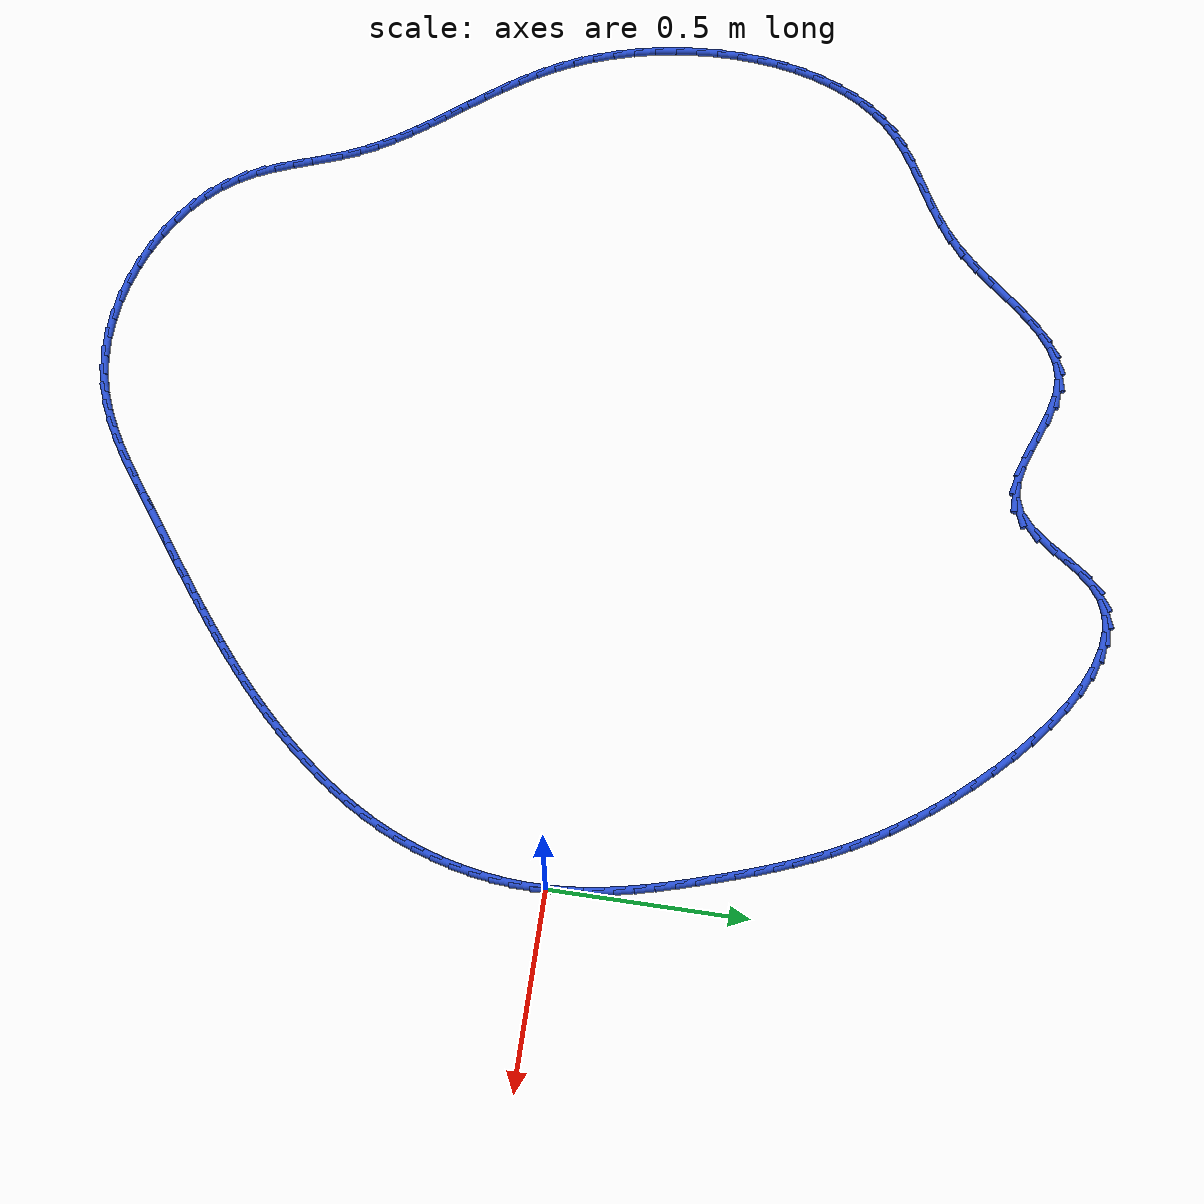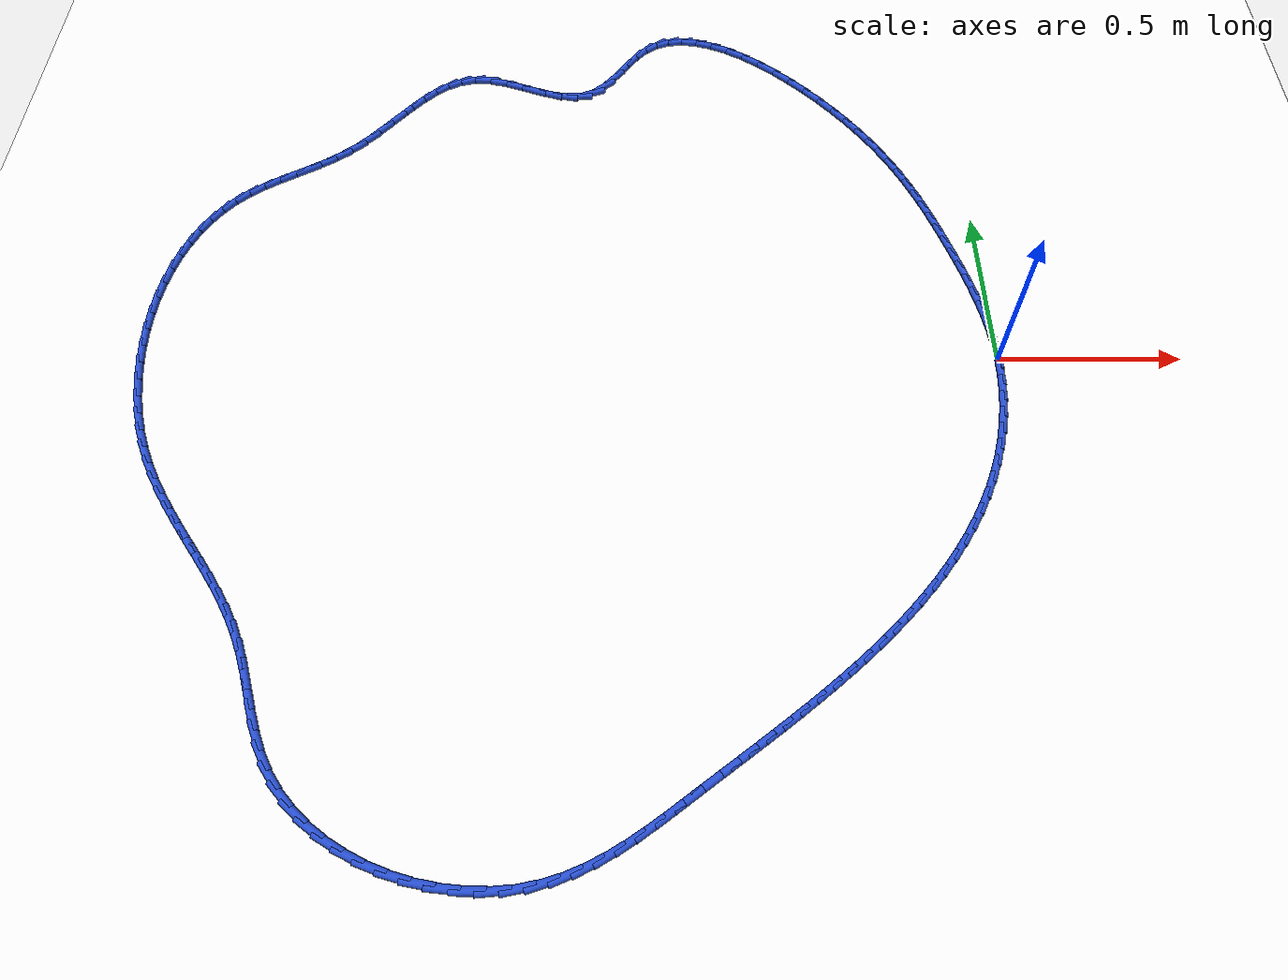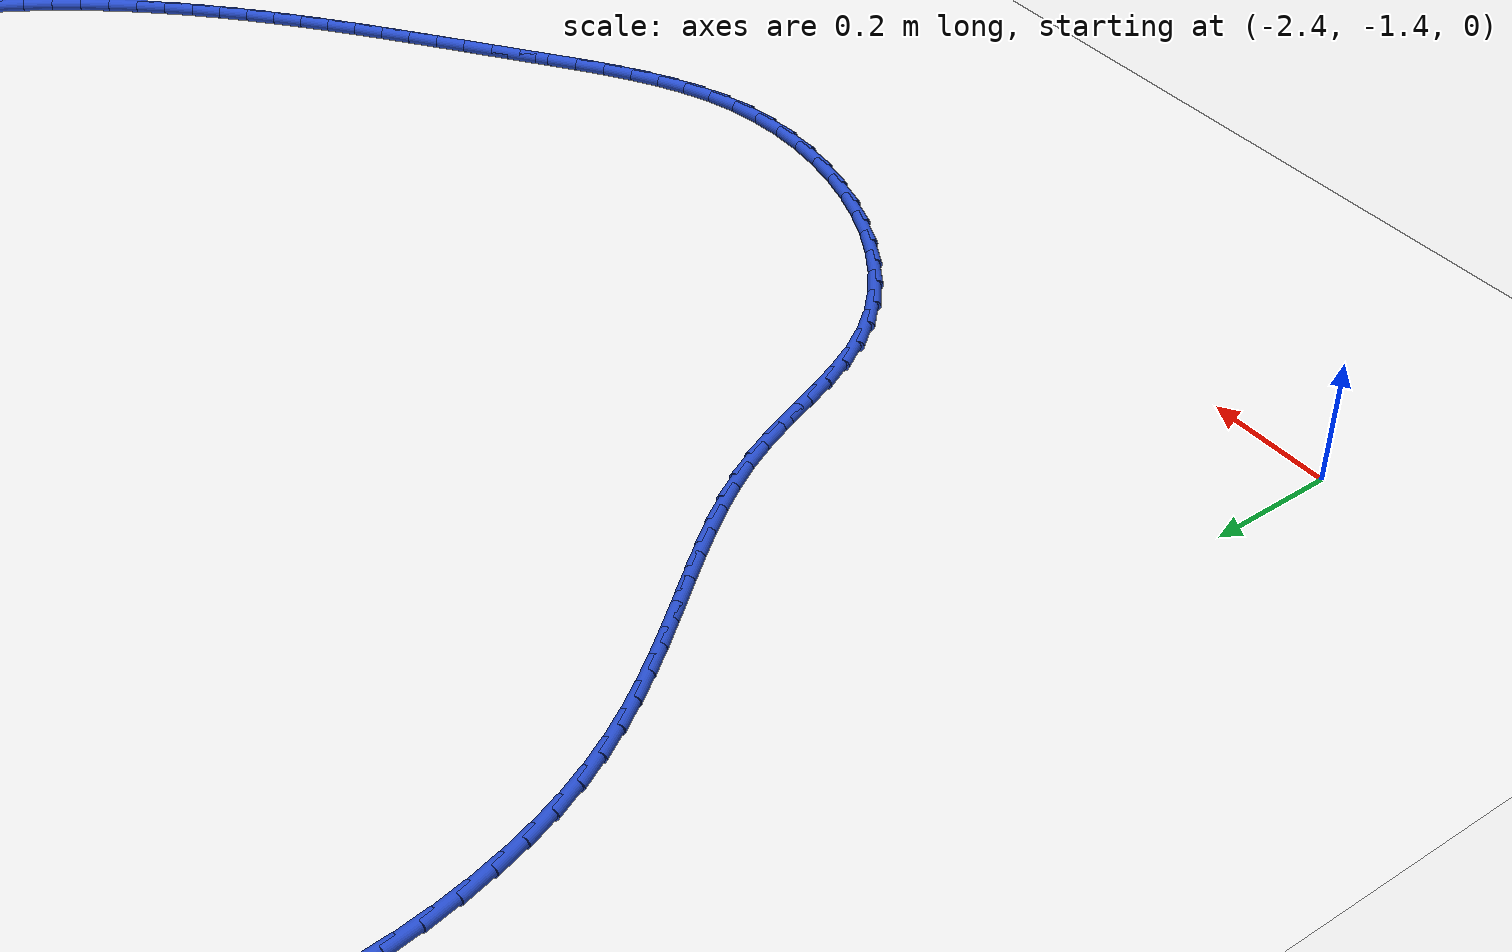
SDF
<sdf version="1.6">
 <world name="default">
  <light name="sun" type="directional">
   <pose>0 0 10 0 -0 0</pose>
   <diffuse>0.8 0.8 0.8 1</diffuse>
   <specular>0.2 0.2 0.2 1</specular>
   <attenuation>
    <range>1000</range>
    <constant>0.9</constant>
    <linear>0.01</linear>
    <quadratic>0.001</quadratic>
   </attenuation>
   <direction>-0.5 0.1 -0.9</direction>
  </light>
  <model name="ground_plane">
   <static>1</static>
   <link name="link">
    <collision name="collision">
     <geometry><plane><normal>0 0 1</normal><size>100 100</size></plane></geometry>
     <surface><friction><ode><mu>100</mu><mu2>50</mu2></ode></friction></surface>
    </collision>
    <visual name="visual">
     <cast_shadows>0</cast_shadows>
     <geometry><plane><normal>0 0 1</normal><size>100 100</size></plane></geometry>
     <material>
      <script><uri>file://media/materials/scripts/gazebo.material</uri><name>Gazebo/WhiteGlow</name></script>
     </material>
    </visual>
   </link>
  </model>
  <gravity>0 0 -9.8</gravity>
  <magnetic_field>6e-06 2.3e-05 -4.2e-05</magnetic_field>
  <atmosphere type="adiabatic"/>
  <physics name="default_physics" default="0" type="ode">
   <max_step_size>0.001</max_step_size>
   <real_time_factor>1</real_time_factor>
   <real_time_update_rate>1000</real_time_update_rate>
  </physics>
  <scene><ambient>0.4 0.4 0.4 1</ambient><background>0.7 0.7 0.7 1</background><shadows>1</shadows></scene>
  <spherical_coordinates>
   <surface_model>EARTH_WGS84</surface_model>
   <latitude_deg>0</latitude_deg>
   <longitude_deg>0</longitude_deg>
   <elevation>0</elevation>
   <heading_deg>0</heading_deg>
  </spherical_coordinates>
  <model name="line">
   <link name="link_0">
    <pose>1.734723475976807e-17 8.326672684688674e-17 0.01 0 1.57 -1.5104639285865724</pose>
    <collision name="collision">
     <geometry><cylinder><radius>0.01</radius><length>0.08</length></cylinder></geometry>
    </collision>
    <visual name="visual">
     <material>
      <script><name>Gazebo/Blue</name><uri>file://media/materials/scripts/gazebo.material</uri></script>
     </material>
     <geometry><cylinder><radius>0.01</radius><length>0.08</length></cylinder></geometry>
    </visual>
   </link>
   <link name="link_1">
    <pose>-0.0030384677710128165 0.050301003999730205 0.01 0 1.57 -1.455969346754686</pose>
    <collision name="collision">
     <geometry><cylinder><radius>0.01</radius><length>0.08</length></cylinder></geometry>
    </collision>
    <visual name="visual">
     <material>
      <script><name>Gazebo/Blue</name><uri>file://media/materials/scripts/gazebo.material</uri></script>
     </material>
     <geometry><cylinder><radius>0.01</radius><length>0.08</length></cylinder></geometry>
    </visual>
   </link>
   <link name="link_2">
    <pose>-0.008818111228535732 0.10041308665040802 0.01 0 1.57 -1.4082257853372324</pose>
    <collision name="collision">
     <geometry><cylinder><radius>0.01</radius><length>0.08</length></cylinder></geometry>
    </collision>
    <visual name="visual">
     <material>
      <script><name>Gazebo/Blue</name><uri>file://media/materials/scripts/gazebo.material</uri></script>
     </material>
     <geometry><cylinder><radius>0.01</radius><length>0.08</length></cylinder></geometry>
    </visual>
   </link>
   <link name="link_3">
    <pose>-0.016990717426067944 0.15024056780476108 0.01 0 1.57 -1.3670323966876647</pose>
    <collision name="collision">
     <geometry><cylinder><radius>0.01</radius><length>0.08</length></cylinder></geometry>
    </collision>
    <visual name="visual">
     <material>
      <script><name>Gazebo/Blue</name><uri>file://media/materials/scripts/gazebo.material</uri></script>
     </material>
     <geometry><cylinder><radius>0.01</radius><length>0.08</length></cylinder></geometry>
    </visual>
   </link>
   <link name="link_4">
    <pose>-0.0272080734171087 0.19968776731551696 0.01 0 1.57 -1.332149021264324</pose>
    <collision name="collision">
     <geometry><cylinder><radius>0.01</radius><length>0.08</length></cylinder></geometry>
    </collision>
    <visual name="visual">
     <material>
      <script><name>Gazebo/Blue</name><uri>file://media/materials/scripts/gazebo.material</uri></script>
     </material>
     <geometry><cylinder><radius>0.01</radius><length>0.08</length></cylinder></geometry>
    </visual>
   </link>
   <link name="link_5">
    <pose>-0.039121966255157195 0.24865900503540295 0.01 0 1.57 -1.303346064127017</pose>
    <collision name="collision">
     <geometry><cylinder><radius>0.01</radius><length>0.08</length></cylinder></geometry>
    </collision>
    <visual name="visual">
     <material>
      <script><name>Gazebo/Blue</name><uri>file://media/materials/scripts/gazebo.material</uri></script>
     </material>
     <geometry><cylinder><radius>0.01</radius><length>0.08</length></cylinder></geometry>
    </visual>
   </link>
   <link name="link_6">
    <pose>-0.052384182993712704 0.2970586008171468 0.01 0 1.57 -1.28044226873742</pose>
    <collision name="collision">
     <geometry><cylinder><radius>0.01</radius><length>0.08</length></cylinder></geometry>
    </collision>
    <visual name="visual">
     <material>
      <script><name>Gazebo/Blue</name><uri>file://media/materials/scripts/gazebo.material</uri></script>
     </material>
     <geometry><cylinder><radius>0.01</radius><length>0.08</length></cylinder></geometry>
    </visual>
   </link>
   <link name="link_7">
    <pose>-0.0666465106862744 0.34479087451347584 0.01 0 1.57 -1.2633341415838295</pose>
    <collision name="collision">
     <geometry><cylinder><radius>0.01</radius><length>0.08</length></cylinder></geometry>
    </collision>
    <visual name="visual">
     <material>
      <script><name>Gazebo/Blue</name><uri>file://media/materials/scripts/gazebo.material</uri></script>
     </material>
     <geometry><cylinder><radius>0.01</radius><length>0.08</length></cylinder></geometry>
    </visual>
   </link>
   <link name="link_8">
    <pose>-0.08156073638634156 0.3917601459771177 0.01 0 1.57 -1.251466192862059</pose>
    <collision name="collision">
     <geometry><cylinder><radius>0.01</radius><length>0.08</length></cylinder></geometry>
    </collision>
    <visual name="visual">
     <material>
      <script><name>Gazebo/Blue</name><uri>file://media/materials/scripts/gazebo.material</uri></script>
     </material>
     <geometry><cylinder><radius>0.01</radius><length>0.08</length></cylinder></geometry>
    </visual>
   </link>
   <link name="link_9">
    <pose>-0.09681104614175311 0.43788289748606046 0.01 0 1.57 -1.2386897921610731</pose>
    <collision name="collision">
     <geometry><cylinder><radius>0.01</radius><length>0.08</length></cylinder></geometry>
    </collision>
    <visual name="visual">
     <material>
      <script><name>Gazebo/Blue</name><uri>file://media/materials/scripts/gazebo.material</uri></script>
     </material>
     <geometry><cylinder><radius>0.01</radius><length>0.08</length></cylinder></geometry>
    </visual>
   </link>
   <link name="link_10">
    <pose>-0.11244404119998534 0.48321166022563466 0.01 0 1.57 -1.2211372713598931</pose>
    <collision name="collision">
     <geometry><cylinder><radius>0.01</radius><length>0.08</length></cylinder></geometry>
    </collision>
    <visual name="visual">
     <material>
      <script><name>Gazebo/Blue</name><uri>file://media/materials/scripts/gazebo.material</uri></script>
     </material>
     <geometry><cylinder><radius>0.01</radius><length>0.08</length></cylinder></geometry>
    </visual>
   </link>
   <link name="link_11">
    <pose>-0.1287335579118084 0.5278842683363002 0.01 0 1.57 -1.1988873354360097</pose>
    <collision name="collision">
     <geometry><cylinder><radius>0.01</radius><length>0.08</length></cylinder></geometry>
    </collision>
    <visual name="visual">
     <material>
      <script><name>Gazebo/Blue</name><uri>file://media/materials/scripts/gazebo.material</uri></script>
     </material>
     <geometry><cylinder><radius>0.01</radius><length>0.08</length></cylinder></geometry>
    </visual>
   </link>
   <link name="link_12">
    <pose>-0.1459569348872716 0.5720398706896564 0.01 0 1.57 -1.172238162713326</pose>
    <collision name="collision">
     <geometry><cylinder><radius>0.01</radius><length>0.08</length></cylinder></geometry>
    </collision>
    <visual name="visual">
     <material>
      <script><name>Gazebo/Blue</name><uri>file://media/materials/scripts/gazebo.material</uri></script>
     </material>
     <geometry><cylinder><radius>0.01</radius><length>0.08</length></cylinder></geometry>
    </visual>
   </link>
   <link name="link_13">
    <pose>-0.16439151073642422 0.6158176161573022 0.01 0 1.57 -1.1416468926700536</pose>
    <collision name="collision">
     <geometry><cylinder><radius>0.01</radius><length>0.08</length></cylinder></geometry>
    </collision>
    <visual name="visual">
     <material>
      <script><name>Gazebo/Blue</name><uri>file://media/materials/scripts/gazebo.material</uri></script>
     </material>
     <geometry><cylinder><radius>0.01</radius><length>0.08</length></cylinder></geometry>
    </visual>
   </link>
   <link name="link_14">
    <pose>-0.1843146240693154 0.6593566536108365 0.01 0 1.57 -1.1077151782764307</pose>
    <collision name="collision">
     <geometry><cylinder><radius>0.01</radius><length>0.08</length></cylinder></geometry>
    </collision>
    <visual name="visual">
     <material>
      <script><name>Gazebo/Blue</name><uri>file://media/materials/scripts/gazebo.material</uri></script>
     </material>
     <geometry><cylinder><radius>0.01</radius><length>0.08</length></cylinder></geometry>
    </visual>
   </link>
   <link name="link_15">
    <pose>-0.2060036134959944 0.7027961319218579 0.01 0 1.57 -1.0711598549641144</pose>
    <collision name="collision">
     <geometry><cylinder><radius>0.01</radius><length>0.08</length></cylinder></geometry>
    </collision>
    <visual name="visual">
     <material>
      <script><name>Gazebo/Blue</name><uri>file://media/materials/scripts/gazebo.material</uri></script>
     </material>
     <geometry><cylinder><radius>0.01</radius><length>0.08</length></cylinder></geometry>
    </visual>
   </link>
   <link name="link_16">
    <pose>-0.2297358176265104 0.7462751999619658 0.01 0 1.57 -1.0327706123056777</pose>
    <collision name="collision">
     <geometry><cylinder><radius>0.01</radius><length>0.08</length></cylinder></geometry>
    </collision>
    <visual name="visual">
     <material>
      <script><name>Gazebo/Blue</name><uri>file://media/materials/scripts/gazebo.material</uri></script>
     </material>
     <geometry><cylinder><radius>0.01</radius><length>0.08</length></cylinder></geometry>
    </visual>
   </link>
   <link name="link_17">
    <pose>-0.25578857507091274 0.7899330066027589 0.01 0 1.57 -0.9933596103766285</pose>
    <collision name="collision">
     <geometry><cylinder><radius>0.01</radius><length>0.08</length></cylinder></geometry>
    </collision>
    <visual name="visual">
     <material>
      <script><name>Gazebo/Blue</name><uri>file://media/materials/scripts/gazebo.material</uri></script>
     </material>
     <geometry><cylinder><radius>0.01</radius><length>0.08</length></cylinder></geometry>
    </visual>
   </link>
   <link name="link_18">
    <pose>-0.28443922443925057 0.8339087007158362 0.01 0 1.57 -0.9537100993118686</pose>
    <collision name="collision">
     <geometry><cylinder><radius>0.01</radius><length>0.08</length></cylinder></geometry>
    </collision>
    <visual name="visual">
     <material>
      <script><name>Gazebo/Blue</name><uri>file://media/materials/scripts/gazebo.material</uri></script>
     </material>
     <geometry><cylinder><radius>0.01</radius><length>0.08</length></cylinder></geometry>
    </visual>
   </link>
   <link name="link_19">
    <pose>-0.3159651043415732 0.8783414311727967 0.01 0 1.57 -0.9145313985060138</pose>
    <collision name="collision">
     <geometry><cylinder><radius>0.01</radius><length>0.08</length></cylinder></geometry>
    </collision>
    <visual name="visual">
     <material>
      <script><name>Gazebo/Blue</name><uri>file://media/materials/scripts/gazebo.material</uri></script>
     </material>
     <geometry><cylinder><radius>0.01</radius><length>0.08</length></cylinder></geometry>
    </visual>
   </link>
   <link name="link_20">
    <pose>-0.35064355338792963 0.9233703468452392 0.01 0 1.57 -0.876389377235969</pose>
    <collision name="collision">
     <geometry><cylinder><radius>0.01</radius><length>0.08</length></cylinder></geometry>
    </collision>
    <visual name="visual">
     <material>
      <script><name>Gazebo/Blue</name><uri>file://media/materials/scripts/gazebo.material</uri></script>
     </material>
     <geometry><cylinder><radius>0.01</radius><length>0.08</length></cylinder></geometry>
    </visual>
   </link>
   <link name="link_21">
    <pose>-0.38872498988956394 0.9690988693357738 0.01 0 1.57 -0.8386794349472038</pose>
    <collision name="collision">
     <geometry><cylinder><radius>0.01</radius><length>0.08</length></cylinder></geometry>
    </collision>
    <visual name="visual">
     <material>
      <script><name>Gazebo/Blue</name><uri>file://media/materials/scripts/gazebo.material</uri></script>
     </material>
     <geometry><cylinder><radius>0.01</radius><length>0.08</length></cylinder></geometry>
    </visual>
   </link>
   <link name="link_22">
    <pose>-0.43001997770106415 1.0150466674958782 0.01 0 1.57 -0.7994188052191216</pose>
    <collision name="collision">
     <geometry><cylinder><radius>0.01</radius><length>0.08</length></cylinder></geometry>
    </collision>
    <visual name="visual">
     <material>
      <script><name>Gazebo/Blue</name><uri>file://media/materials/scripts/gazebo.material</uri></script>
     </material>
     <geometry><cylinder><radius>0.01</radius><length>0.08</length></cylinder></geometry>
    </visual>
   </link>
   <link name="link_23">
    <pose>-0.4739804719015362 1.0602574826148556 0.01 0 1.57 -0.7567828916099218</pose>
    <collision name="collision">
     <geometry><cylinder><radius>0.01</radius><length>0.08</length></cylinder></geometry>
    </collision>
    <visual name="visual">
     <material>
      <script><name>Gazebo/Blue</name><uri>file://media/materials/scripts/gazebo.material</uri></script>
     </material>
     <geometry><cylinder><radius>0.01</radius><length>0.08</length></cylinder></geometry>
    </visual>
   </link>
   <link name="link_24">
    <pose>-0.520047969124187 1.1037611760576984 0.01 0 1.57 -0.7087802669123512</pose>
    <collision name="collision">
     <geometry><cylinder><radius>0.01</radius><length>0.08</length></cylinder></geometry>
    </collision>
    <visual name="visual">
     <material>
      <script><name>Gazebo/Blue</name><uri>file://media/materials/scripts/gazebo.material</uri></script>
     </material>
     <geometry><cylinder><radius>0.01</radius><length>0.08</length></cylinder></geometry>
    </visual>
   </link>
   <link name="link_25">
    <pose>-0.5676639660022248 1.1445876091894003 0.01 0 1.57 -0.6529731325342216</pose>
    <collision name="collision">
     <geometry><cylinder><radius>0.01</radius><length>0.08</length></cylinder></geometry>
    </collision>
    <visual name="visual">
     <material>
      <script><name>Gazebo/Blue</name><uri>file://media/materials/scripts/gazebo.material</uri></script>
     </material>
     <geometry><cylinder><radius>0.01</radius><length>0.08</length></cylinder></geometry>
    </visual>
   </link>
   <link name="link_26">
    <pose>-0.6162699591688562 1.1817666433749532 0.01 0 1.57 -0.5861627510612983</pose>
    <collision name="collision">
     <geometry><cylinder><radius>0.01</radius><length>0.08</length></cylinder></geometry>
    </collision>
    <visual name="visual">
     <material>
      <script><name>Gazebo/Blue</name><uri>file://media/materials/scripts/gazebo.material</uri></script>
     </material>
     <geometry><cylinder><radius>0.01</radius><length>0.08</length></cylinder></geometry>
    </visual>
   </link>
   <link name="link_27">
    <pose>-0.6653074452572895 1.2143281399793517 0.01 0 1.57 -0.5039893011024552</pose>
    <collision name="collision">
     <geometry><cylinder><radius>0.01</radius><length>0.08</length></cylinder></geometry>
    </collision>
    <visual name="visual">
     <material>
      <script><name>Gazebo/Blue</name><uri>file://media/materials/scripts/gazebo.material</uri></script>
     </material>
     <geometry><cylinder><radius>0.01</radius><length>0.08</length></cylinder></geometry>
    </visual>
   </link>
   <link name="link_28">
    <pose>-0.7142179209007314 1.2413019603675877 0.01 0 1.57 -0.4004716892429692</pose>
    <collision name="collision">
     <geometry><cylinder><radius>0.01</radius><length>0.08</length></cylinder></geometry>
    </collision>
    <visual name="visual">
     <material>
      <script><name>Gazebo/Blue</name><uri>file://media/materials/scripts/gazebo.material</uri></script>
     </material>
     <geometry><cylinder><radius>0.01</radius><length>0.08</length></cylinder></geometry>
    </visual>
   </link>
   <link name="link_29">
    <pose>-0.7624428827323899 1.2617179659046545 0.01 0 1.57 -0.26773864782263546</pose>
    <collision name="collision">
     <geometry><cylinder><radius>0.01</radius><length>0.08</length></cylinder></geometry>
    </collision>
    <visual name="visual">
     <material>
      <script><name>Gazebo/Blue</name><uri>file://media/materials/scripts/gazebo.material</uri></script>
     </material>
     <geometry><cylinder><radius>0.01</radius><length>0.08</length></cylinder></geometry>
    </visual>
   </link>
   <link name="link_30">
    <pose>-0.8094238273854722 1.2746060179555454 0.01 0 1.57 -0.09686529040320005</pose>
    <collision name="collision">
     <geometry><cylinder><radius>0.01</radius><length>0.08</length></cylinder></geometry>
    </collision>
    <visual name="visual">
     <material>
      <script><name>Gazebo/Blue</name><uri>file://media/materials/scripts/gazebo.material</uri></script>
     </material>
     <geometry><cylinder><radius>0.01</radius><length>0.08</length></cylinder></geometry>
    </visual>
   </link>
   <link name="link_31">
    <pose>-0.854602251493186 1.278995977885253 0.01 0 1.57 0.11805150080588234</pose>
    <collision name="collision">
     <geometry><cylinder><radius>0.01</radius><length>0.08</length></cylinder></geometry>
    </collision>
    <visual name="visual">
     <material>
      <script><name>Gazebo/Blue</name><uri>file://media/materials/scripts/gazebo.material</uri></script>
     </material>
     <geometry><cylinder><radius>0.01</radius><length>0.08</length></cylinder></geometry>
    </visual>
   </link>
   <link name="link_32">
    <pose>-0.8974196516887383 1.273917707058771 0.01 0 1.57 0.3709087221486461</pose>
    <collision name="collision">
     <geometry><cylinder><radius>0.01</radius><length>0.08</length></cylinder></geometry>
    </collision>
    <visual name="visual">
     <material>
      <script><name>Gazebo/Blue</name><uri>file://media/materials/scripts/gazebo.material</uri></script>
     </material>
     <geometry><cylinder><radius>0.01</radius><length>0.08</length></cylinder></geometry>
    </visual>
   </link>
   <link name="link_33">
    <pose>-0.9373175246053365 1.2584010668410917 0.01 0 1.57 0.6364861758430974</pose>
    <collision name="collision">
     <geometry><cylinder><radius>0.01</radius><length>0.08</length></cylinder></geometry>
    </collision>
    <visual name="visual">
     <material>
      <script><name>Gazebo/Blue</name><uri>file://media/materials/scripts/gazebo.material</uri></script>
     </material>
     <geometry><cylinder><radius>0.01</radius><length>0.08</length></cylinder></geometry>
    </visual>
   </link>
   <link name="link_34">
    <pose>-0.9737394846749473 1.2314817289238185 0.01 0 1.57 0.8505760748625117</pose>
    <collision name="collision">
     <geometry><cylinder><radius>0.01</radius><length>0.08</length></cylinder></geometry>
    </collision>
    <visual name="visual">
     <material>
      <script><name>Gazebo/Blue</name><uri>file://media/materials/scripts/gazebo.material</uri></script>
     </material>
     <geometry><cylinder><radius>0.01</radius><length>0.08</length></cylinder></geometry>
    </visual>
   </link>
   <link name="link_35">
    <pose>-1.006740310337946 1.1938721355073316 0.01 0 1.57 0.9513793097877986</pose>
    <collision name="collision">
     <geometry><cylinder><radius>0.01</radius><length>0.08</length></cylinder></geometry>
    </collision>
    <visual name="visual">
     <material>
      <script><name>Gazebo/Blue</name><uri>file://media/materials/scripts/gazebo.material</uri></script>
     </material>
     <geometry><cylinder><radius>0.01</radius><length>0.08</length></cylinder></geometry>
    </visual>
   </link>
   <link name="link_36">
    <pose>-1.0378282265763445 1.1502723593847102 0.01 0 1.57 0.9619257183664889</pose>
    <collision name="collision">
     <geometry><cylinder><radius>0.01</radius><length>0.08</length></cylinder></geometry>
    </collision>
    <visual name="visual">
     <material>
      <script><name>Gazebo/Blue</name><uri>file://media/materials/scripts/gazebo.material</uri></script>
     </material>
     <geometry><cylinder><radius>0.01</radius><length>0.08</length></cylinder></geometry>
    </visual>
   </link>
   <link name="link_37">
    <pose>-1.0687228446479429 1.1059624261412893 0.01 0 1.57 0.8864803135045498</pose>
    <collision name="collision">
     <geometry><cylinder><radius>0.01</radius><length>0.08</length></cylinder></geometry>
    </collision>
    <visual name="visual">
     <material>
      <script><name>Gazebo/Blue</name><uri>file://media/materials/scripts/gazebo.material</uri></script>
     </material>
     <geometry><cylinder><radius>0.01</radius><length>0.08</length></cylinder></geometry>
    </visual>
   </link>
   <link name="link_38">
    <pose>-1.101143775810542 1.066222361362403 0.01 0 1.57 0.6975082273294769</pose>
    <collision name="collision">
     <geometry><cylinder><radius>0.01</radius><length>0.08</length></cylinder></geometry>
    </collision>
    <visual name="visual">
     <material>
      <script><name>Gazebo/Blue</name><uri>file://media/materials/scripts/gazebo.material</uri></script>
     </material>
     <geometry><cylinder><radius>0.01</radius><length>0.08</length></cylinder></geometry>
    </visual>
   </link>
   <link name="link_39">
    <pose>-1.1368106313219417 1.0363321906333856 0.01 0 1.57 0.35601924894925785</pose>
    <collision name="collision">
     <geometry><cylinder><radius>0.01</radius><length>0.08</length></cylinder></geometry>
    </collision>
    <visual name="visual">
     <material>
      <script><name>Gazebo/Blue</name><uri>file://media/materials/scripts/gazebo.material</uri></script>
     </material>
     <geometry><cylinder><radius>0.01</radius><length>0.08</length></cylinder></geometry>
    </visual>
   </link>
   <link name="link_40">
    <pose>-1.177342311507074 1.0212598819654546 0.01 0 1.57 0.006444618043829705</pose>
    <collision name="collision">
     <geometry><cylinder><radius>0.01</radius><length>0.08</length></cylinder></geometry>
    </collision>
    <visual name="visual">
     <material>
      <script><name>Gazebo/Blue</name><uri>file://media/materials/scripts/gazebo.material</uri></script>
     </material>
     <geometry><cylinder><radius>0.01</radius><length>0.08</length></cylinder></geometry>
    </visual>
   </link>
   <link name="link_41">
    <pose>-1.2227420854245863 1.0209672937125696 0.01 0 1.57 -0.2095694489529108</pose>
    <collision name="collision">
     <geometry><cylinder><radius>0.01</radius><length>0.08</length></cylinder></geometry>
    </collision>
    <visual name="visual">
     <material>
      <script><name>Gazebo/Blue</name><uri>file://media/materials/scripts/gazebo.material</uri></script>
     </material>
     <geometry><cylinder><radius>0.01</radius><length>0.08</length></cylinder></geometry>
    </visual>
   </link>
   <link name="link_42">
    <pose>-1.2717114577143405 1.0313827057975609 0.01 0 1.57 -0.31944922550888594</pose>
    <collision name="collision">
     <geometry><cylinder><radius>0.01</radius><length>0.08</length></cylinder></geometry>
    </collision>
    <visual name="visual">
     <material>
      <script><name>Gazebo/Blue</name><uri>file://media/materials/scripts/gazebo.material</uri></script>
     </material>
     <geometry><cylinder><radius>0.01</radius><length>0.08</length></cylinder></geometry>
    </visual>
   </link>
   <link name="link_43">
    <pose>-1.3229149150229103 1.0483196961456123 0.01 0 1.57 -0.3542853061502275</pose>
    <collision name="collision">
     <geometry><cylinder><radius>0.01</radius><length>0.08</length></cylinder></geometry>
    </collision>
    <visual name="visual">
     <material>
      <script><name>Gazebo/Blue</name><uri>file://media/materials/scripts/gazebo.material</uri></script>
     </material>
     <geometry><cylinder><radius>0.01</radius><length>0.08</length></cylinder></geometry>
    </visual>
   </link>
   <link name="link_44">
    <pose>-1.3750169439968674 1.067591842681907 0.01 0 1.57 -0.32521631034067916</pose>
    <collision name="collision">
     <geometry><cylinder><radius>0.01</radius><length>0.08</length></cylinder></geometry>
    </collision>
    <visual name="visual">
     <material>
      <script><name>Gazebo/Blue</name><uri>file://media/materials/scripts/gazebo.material</uri></script>
     </material>
     <geometry><cylinder><radius>0.01</radius><length>0.08</length></cylinder></geometry>
    </visual>
   </link>
   <link name="link_45">
    <pose>-1.4266820312827861 1.0850127233316291 0.01 0 1.57 -0.2243142213830926</pose>
    <collision name="collision">
     <geometry><cylinder><radius>0.01</radius><length>0.08</length></cylinder></geometry>
    </collision>
    <visual name="visual">
     <material>
      <script><name>Gazebo/Blue</name><uri>file://media/materials/scripts/gazebo.material</uri></script>
     </material>
     <geometry><cylinder><radius>0.01</radius><length>0.08</length></cylinder></geometry>
    </visual>
   </link>
   <link name="link_46">
    <pose>-1.4765746635272377 1.0963959160199614 0.01 0 1.57 -0.025791967116371044</pose>
    <collision name="collision">
     <geometry><cylinder><radius>0.01</radius><length>0.08</length></cylinder></geometry>
    </collision>
    <visual name="visual">
     <material>
      <script><name>Gazebo/Blue</name><uri>file://media/materials/scripts/gazebo.material</uri></script>
     </material>
     <geometry><cylinder><radius>0.01</radius><length>0.08</length></cylinder></geometry>
    </visual>
   </link>
   <link name="link_47">
    <pose>-1.5233753430168322 1.0976032653381331 0.01 0 1.57 0.24336707877210206</pose>
    <collision name="collision">
     <geometry><cylinder><radius>0.01</radius><length>0.08</length></cylinder></geometry>
    </collision>
    <visual name="visual">
     <material>
      <script><name>Gazebo/Blue</name><uri>file://media/materials/scripts/gazebo.material</uri></script>
     </material>
     <geometry><cylinder><radius>0.01</radius><length>0.08</length></cylinder></geometry>
    </visual>
   </link>
   <link name="link_48">
    <pose>-1.5665560770273415 1.0868819908544052 0.01 0 1.57 0.4811537703098909</pose>
    <collision name="collision">
     <geometry><cylinder><radius>0.01</radius><length>0.08</length></cylinder></geometry>
    </collision>
    <visual name="visual">
     <material>
      <script><name>Gazebo/Blue</name><uri>file://media/materials/scripts/gazebo.material</uri></script>
     </material>
     <geometry><cylinder><radius>0.01</radius><length>0.08</length></cylinder></geometry>
    </visual>
   </link>
   <link name="link_49">
    <pose>-1.6067270898729125 1.0659095803968053 0.01 0 1.57 0.6582996687488513</pose>
    <collision name="collision">
     <geometry><cylinder><radius>0.01</radius><length>0.08</length></cylinder></geometry>
    </collision>
    <visual name="visual">
     <material>
      <script><name>Gazebo/Blue</name><uri>file://media/materials/scripts/gazebo.material</uri></script>
     </material>
     <geometry><cylinder><radius>0.01</radius><length>0.08</length></cylinder></geometry>
    </visual>
   </link>
   <link name="link_50">
    <pose>-1.6445868454936012 1.0366294513813086 0.01 0 1.57 0.7770172147172573</pose>
    <collision name="collision">
     <geometry><cylinder><radius>0.01</radius><length>0.08</length></cylinder></geometry>
    </collision>
    <visual name="visual">
     <material>
      <script><name>Gazebo/Blue</name><uri>file://media/materials/scripts/gazebo.material</uri></script>
     </material>
     <geometry><cylinder><radius>0.01</radius><length>0.08</length></cylinder></geometry>
    </visual>
   </link>
   <link name="link_51">
    <pose>-1.6808338078294642 1.0009850212238924 0.01 0 1.57 0.8480852810801377</pose>
    <collision name="collision">
     <geometry><cylinder><radius>0.01</radius><length>0.08</length></cylinder></geometry>
    </collision>
    <visual name="visual">
     <material>
      <script><name>Gazebo/Blue</name><uri>file://media/materials/scripts/gazebo.material</uri></script>
     </material>
     <geometry><cylinder><radius>0.01</radius><length>0.08</length></cylinder></geometry>
    </visual>
   </link>
   <link name="link_52">
    <pose>-1.7161664408205572 0.9609197073405321 0.01 0 1.57 0.8807309648319773</pose>
    <collision name="collision">
     <geometry><cylinder><radius>0.01</radius><length>0.08</length></cylinder></geometry>
    </collision>
    <visual name="visual">
     <material>
      <script><name>Gazebo/Blue</name><uri>file://media/materials/scripts/gazebo.material</uri></script>
     </material>
     <geometry><cylinder><radius>0.01</radius><length>0.08</length></cylinder></geometry>
    </visual>
   </link>
   <link name="link_53">
    <pose>-1.7512832084069363 0.9183769271472035 0.01 0 1.57 0.8801545260970428</pose>
    <collision name="collision">
     <geometry><cylinder><radius>0.01</radius><length>0.08</length></cylinder></geometry>
    </collision>
    <visual name="visual">
     <material>
      <script><name>Gazebo/Blue</name><uri>file://media/materials/scripts/gazebo.material</uri></script>
     </material>
     <geometry><cylinder><radius>0.01</radius><length>0.08</length></cylinder></geometry>
    </visual>
   </link>
   <link name="link_54">
    <pose>-1.7868825745286583 0.8753000980598824 0.01 0 1.57 0.8476143012716058</pose>
    <collision name="collision">
     <geometry><cylinder><radius>0.01</radius><length>0.08</length></cylinder></geometry>
    </collision>
    <visual name="visual">
     <material>
      <script><name>Gazebo/Blue</name><uri>file://media/materials/scripts/gazebo.material</uri></script>
     </material>
     <geometry><cylinder><radius>0.01</radius><length>0.08</length></cylinder></geometry>
    </visual>
   </link>
   <link name="link_55">
    <pose>-1.8236630031257786 0.8336326374945455 0.01 0 1.57 0.7809125546839047</pose>
    <collision name="collision">
     <geometry><cylinder><radius>0.01</radius><length>0.08</length></cylinder></geometry>
    </collision>
    <visual name="visual">
     <material>
      <script><name>Gazebo/Blue</name><uri>file://media/materials/scripts/gazebo.material</uri></script>
     </material>
     <geometry><cylinder><radius>0.01</radius><length>0.08</length></cylinder></geometry>
    </visual>
   </link>
   <link name="link_56">
    <pose>-1.8623229581383531 0.7953179628671682 0.01 0 1.57 0.6824615897221823</pose>
    <collision name="collision">
     <geometry><cylinder><radius>0.01</radius><length>0.08</length></cylinder></geometry>
    </collision>
    <visual name="visual">
     <material>
      <script><name>Gazebo/Blue</name><uri>file://media/materials/scripts/gazebo.material</uri></script>
     </material>
     <geometry><cylinder><radius>0.01</radius><length>0.08</length></cylinder></geometry>
    </visual>
   </link>
   <link name="link_57">
    <pose>-1.903387301612877 0.7619432951352602 0.01 0 1.57 0.5943881100713446</pose>
    <collision name="collision">
     <geometry><cylinder><radius>0.01</radius><length>0.08</length></cylinder></geometry>
    </collision>
    <visual name="visual">
     <material>
      <script><name>Gazebo/Blue</name><uri>file://media/materials/scripts/gazebo.material</uri></script>
     </material>
     <geometry><cylinder><radius>0.01</radius><length>0.08</length></cylinder></geometry>
    </visual>
   </link>
   <link name="link_58">
    <pose>-1.9463217225282812 0.7329226433873264 0.01 0 1.57 0.5362124962702877</pose>
    <collision name="collision">
     <geometry><cylinder><radius>0.01</radius><length>0.08</length></cylinder></geometry>
    </collision>
    <visual name="visual">
     <material>
      <script><name>Gazebo/Blue</name><uri>file://media/materials/scripts/gazebo.material</uri></script>
     </material>
     <geometry><cylinder><radius>0.01</radius><length>0.08</length></cylinder></geometry>
    </visual>
   </link>
   <link name="link_59">
    <pose>-1.990192517689697 0.7068505436351241 0.01 0 1.57 0.5098250113790918</pose>
    <collision name="collision">
     <geometry><cylinder><radius>0.01</radius><length>0.08</length></cylinder></geometry>
    </collision>
    <visual name="visual">
     <material>
      <script><name>Gazebo/Blue</name><uri>file://media/materials/scripts/gazebo.material</uri></script>
     </material>
     <geometry><cylinder><radius>0.01</radius><length>0.08</length></cylinder></geometry>
    </visual>
   </link>
   <link name="link_60">
    <pose>-2.034065250260231 0.6823200266033079 0.01 0 1.57 0.5166607003762833</pose>
    <collision name="collision">
     <geometry><cylinder><radius>0.01</radius><length>0.08</length></cylinder></geometry>
    </collision>
    <visual name="visual">
     <material>
      <script><name>Gazebo/Blue</name><uri>file://media/materials/scripts/gazebo.material</uri></script>
     </material>
     <geometry><cylinder><radius>0.01</radius><length>0.08</length></cylinder></geometry>
    </visual>
   </link>
   <link name="link_61">
    <pose>-2.077005483402991 0.6579241230165326 0.01 0 1.57 0.5585546495133832</pose>
    <collision name="collision">
     <geometry><cylinder><radius>0.01</radius><length>0.08</length></cylinder></geometry>
    </collision>
    <visual name="visual">
     <material>
      <script><name>Gazebo/Blue</name><uri>file://media/materials/scripts/gazebo.material</uri></script>
     </material>
     <geometry><cylinder><radius>0.01</radius><length>0.08</length></cylinder></geometry>
    </visual>
   </link>
   <link name="link_62">
    <pose>-2.118078780281083 0.6322558635994527 0.01 0 1.57 0.6375152459106737</pose>
    <collision name="collision">
     <geometry><cylinder><radius>0.01</radius><length>0.08</length></cylinder></geometry>
    </collision>
    <visual name="visual">
     <material>
      <script><name>Gazebo/Blue</name><uri>file://media/materials/scripts/gazebo.material</uri></script>
     </material>
     <geometry><cylinder><radius>0.01</radius><length>0.08</length></cylinder></geometry>
    </visual>
   </link>
   <link name="link_63">
    <pose>-2.156350704057612 0.6039082790767228 0.01 0 1.57 0.7508035206176465</pose>
    <collision name="collision">
     <geometry><cylinder><radius>0.01</radius><length>0.08</length></cylinder></geometry>
    </collision>
    <visual name="visual">
     <material>
      <script><name>Gazebo/Blue</name><uri>file://media/materials/scripts/gazebo.material</uri></script>
     </material>
     <geometry><cylinder><radius>0.01</radius><length>0.08</length></cylinder></geometry>
    </visual>
   </link>
   <link name="link_64">
    <pose>-2.1909634653442778 0.57161116488495 0.01 0 1.57 0.8698479731634604</pose>
    <collision name="collision">
     <geometry><cylinder><radius>0.01</radius><length>0.08</length></cylinder></geometry>
    </collision>
    <visual name="visual">
     <material>
      <script><name>Gazebo/Blue</name><uri>file://media/materials/scripts/gazebo.material</uri></script>
     </material>
     <geometry><cylinder><radius>0.01</radius><length>0.08</length></cylinder></geometry>
    </visual>
   </link>
   <link name="link_65">
    <pose>-2.2216838471331766 0.5352087627113296 0.01 0 1.57 0.9801697368502972</pose>
    <collision name="collision">
     <geometry><cylinder><radius>0.01</radius><length>0.08</length></cylinder></geometry>
    </collision>
    <visual name="visual">
     <material>
      <script><name>Gazebo/Blue</name><uri>file://media/materials/scripts/gazebo.material</uri></script>
     </material>
     <geometry><cylinder><radius>0.01</radius><length>0.08</length></cylinder></geometry>
    </visual>
   </link>
   <link name="link_66">
    <pose>-2.248583037072549 0.49508847407263473 0.01 0 1.57 1.0812076367470602</pose>
    <collision name="collision">
     <geometry><cylinder><radius>0.01</radius><length>0.08</length></cylinder></geometry>
    </collision>
    <visual name="visual">
     <material>
      <script><name>Gazebo/Blue</name><uri>file://media/materials/scripts/gazebo.material</uri></script>
     </material>
     <geometry><cylinder><radius>0.01</radius><length>0.08</length></cylinder></geometry>
    </visual>
   </link>
   <link name="link_67">
    <pose>-2.2717342684287334 0.4516413505532575 0.01 0 1.57 1.1732474148710617</pose>
    <collision name="collision">
     <geometry><cylinder><radius>0.01</radius><length>0.08</length></cylinder></geometry>
    </collision>
    <visual name="visual">
     <material>
      <script><name>Gazebo/Blue</name><uri>file://media/materials/scripts/gazebo.material</uri></script>
     </material>
     <geometry><cylinder><radius>0.01</radius><length>0.08</length></cylinder></geometry>
    </visual>
   </link>
   <link name="link_68">
    <pose>-2.2912107744680705 0.40525844373759123 0.01 0 1.57 1.2570537970908655</pose>
    <collision name="collision">
     <geometry><cylinder><radius>0.01</radius><length>0.08</length></cylinder></geometry>
    </collision>
    <visual name="visual">
     <material>
      <script><name>Gazebo/Blue</name><uri>file://media/materials/scripts/gazebo.material</uri></script>
     </material>
     <geometry><cylinder><radius>0.01</radius><length>0.08</length></cylinder></geometry>
    </visual>
   </link>
   <link name="link_69">
    <pose>-2.3070857884568983 0.3563308052100277 0.01 0 1.57 1.3336371469000525</pose>
    <collision name="collision">
     <geometry><cylinder><radius>0.01</radius><length>0.08</length></cylinder></geometry>
    </collision>
    <visual name="visual">
     <material>
      <script><name>Gazebo/Blue</name><uri>file://media/materials/scripts/gazebo.material</uri></script>
     </material>
     <geometry><cylinder><radius>0.01</radius><length>0.08</length></cylinder></geometry>
    </visual>
   </link>
   <link name="link_70">
    <pose>-2.319432543661557 0.3052494865549594 0.01 0 1.57 1.4040939690445866</pose>
    <collision name="collision">
     <geometry><cylinder><radius>0.01</radius><length>0.08</length></cylinder></geometry>
    </collision>
    <visual name="visual">
     <material>
      <script><name>Gazebo/Blue</name><uri>file://media/materials/scripts/gazebo.material</uri></script>
     </material>
     <geometry><cylinder><radius>0.01</radius><length>0.08</length></cylinder></geometry>
    </visual>
   </link>
   <link name="link_71">
    <pose>-2.3283242733483855 0.25240553935677834 0.01 0 1.57 1.4695138243402548</pose>
    <collision name="collision">
     <geometry><cylinder><radius>0.01</radius><length>0.08</length></cylinder></geometry>
    </collision>
    <visual name="visual">
     <material>
      <script><name>Gazebo/Blue</name><uri>file://media/materials/scripts/gazebo.material</uri></script>
     </material>
     <geometry><cylinder><radius>0.01</radius><length>0.08</length></cylinder></geometry>
    </visual>
   </link>
   <link name="link_72">
    <pose>-2.3338342107837224 0.19819001519987756 0.01 0 1.57 1.5309345544895907</pose>
    <collision name="collision">
     <geometry><cylinder><radius>0.01</radius><length>0.08</length></cylinder></geometry>
    </collision>
    <visual name="visual">
     <material>
      <script><name>Gazebo/Blue</name><uri>file://media/materials/scripts/gazebo.material</uri></script>
     </material>
     <geometry><cylinder><radius>0.01</radius><length>0.08</length></cylinder></geometry>
    </visual>
   </link>
   <link name="link_73">
    <pose>-2.3360355892339073 0.14299396566864922 0.01 0 1.57 -1.5522641192050364</pose>
    <collision name="collision">
     <geometry><cylinder><radius>0.01</radius><length>0.08</length></cylinder></geometry>
    </collision>
    <visual name="visual">
     <material>
      <script><name>Gazebo/Blue</name><uri>file://media/materials/scripts/gazebo.material</uri></script>
     </material>
     <geometry><cylinder><radius>0.01</radius><length>0.08</length></cylinder></geometry>
    </visual>
   </link>
   <link name="link_74">
    <pose>-2.33500164196528 0.08720844234748584 0.01 0 1.57 -1.4959854357371398</pose>
    <collision name="collision">
     <geometry><cylinder><radius>0.01</radius><length>0.08</length></cylinder></geometry>
    </collision>
    <visual name="visual">
     <material>
      <script><name>Gazebo/Blue</name><uri>file://media/materials/scripts/gazebo.material</uri></script>
     </material>
     <geometry><cylinder><radius>0.01</radius><length>0.08</length></cylinder></geometry>
    </visual>
   </link>
   <link name="link_75">
    <pose>-2.330805602244179 0.03122449682077951 0.01 0 1.57 -1.4409568402950295</pose>
    <collision name="collision">
     <geometry><cylinder><radius>0.01</radius><length>0.08</length></cylinder></geometry>
    </collision>
    <visual name="visual">
     <material>
      <script><name>Gazebo/Blue</name><uri>file://media/materials/scripts/gazebo.material</uri></script>
     </material>
     <geometry><cylinder><radius>0.01</radius><length>0.08</length></cylinder></geometry>
    </visual>
   </link>
   <link name="link_76">
    <pose>-2.3235207033369445 -0.024566819327077632 0.01 0 1.57 -1.3863393054335211</pose>
    <collision name="collision">
     <geometry><cylinder><radius>0.01</radius><length>0.08</length></cylinder></geometry>
    </collision>
    <visual name="visual">
     <material>
      <script><name>Gazebo/Blue</name><uri>file://media/materials/scripts/gazebo.material</uri></script>
     </material>
     <geometry><cylinder><radius>0.01</radius><length>0.08</length></cylinder></geometry>
    </visual>
   </link>
   <link name="link_77">
    <pose>-2.3132201785099142 -0.07977445451169281 0.01 0 1.57 -1.3312970714176182</pose>
    <collision name="collision">
     <geometry><cylinder><radius>0.01</radius><length>0.08</length></cylinder></geometry>
    </collision>
    <visual name="visual">
     <material>
      <script><name>Gazebo/Blue</name><uri>file://media/materials/scripts/gazebo.material</uri></script>
     </material>
     <geometry><cylinder><radius>0.01</radius><length>0.08</length></cylinder></geometry>
    </visual>
   </link>
   <link name="link_78">
    <pose>-2.2999772610294293 -0.13400735714867262 0.01 0 1.57 -1.2749732155554854</pose>
    <collision name="collision">
     <geometry><cylinder><radius>0.01</radius><length>0.08</length></cylinder></geometry>
    </collision>
    <visual name="visual">
     <material>
      <script><name>Gazebo/Blue</name><uri>file://media/materials/scripts/gazebo.material</uri></script>
     </material>
     <geometry><cylinder><radius>0.01</radius><length>0.08</length></cylinder></geometry>
    </visual>
   </link>
   <link name="link_79">
    <pose>-2.2838651841618276 -0.18687447565362653 0.01 0 1.57 -1.216464623546199</pose>
    <collision name="collision">
     <geometry><cylinder><radius>0.01</radius><length>0.08</length></cylinder></geometry>
    </collision>
    <visual name="visual">
     <material>
      <script><name>Gazebo/Blue</name><uri>file://media/materials/scripts/gazebo.material</uri></script>
     </material>
     <geometry><cylinder><radius>0.01</radius><length>0.08</length></cylinder></geometry>
    </visual>
   </link>
   <link name="link_80">
    <pose>-2.2649571811734495 -0.2379847584421604 0.01 0 1.57 -1.154801436627068</pose>
    <collision name="collision">
     <geometry><cylinder><radius>0.01</radius><length>0.08</length></cylinder></geometry>
    </collision>
    <visual name="visual">
     <material>
      <script><name>Gazebo/Blue</name><uri>file://media/materials/scripts/gazebo.material</uri></script>
     </material>
     <geometry><cylinder><radius>0.01</radius><length>0.08</length></cylinder></geometry>
    </visual>
   </link>
   <link name="link_81">
    <pose>-2.2433266038239625 -0.2869473902744213 0.01 0 1.57 -1.0919396306300397</pose>
    <collision name="collision">
     <geometry><cylinder><radius>0.01</radius><length>0.08</length></cylinder></geometry>
    </collision>
    <visual name="visual">
     <material>
      <script><name>Gazebo/Blue</name><uri>file://media/materials/scripts/gazebo.material</uri></script>
     </material>
     <geometry><cylinder><radius>0.01</radius><length>0.08</length></cylinder></geometry>
    </visual>
   </link>
   <link name="link_82">
    <pose>-2.2191343981389853 -0.3335462697632841 0.01 0 1.57 -1.0362052882940918</pose>
    <collision name="collision">
     <geometry><cylinder><radius>0.01</radius><length>0.08</length></cylinder></geometry>
    </collision>
    <visual name="visual">
     <material>
      <script><name>Gazebo/Blue</name><uri>file://media/materials/scripts/gazebo.material</uri></script>
     </material>
     <geometry><cylinder><radius>0.01</radius><length>0.08</length></cylinder></geometry>
    </visual>
   </link>
   <link name="link_83">
    <pose>-2.192784145702399 -0.37804925177990406 0.01 0 1.57 -0.989989534091592</pose>
    <collision name="collision">
     <geometry><cylinder><radius>0.01</radius><length>0.08</length></cylinder></geometry>
    </collision>
    <visual name="visual">
     <material>
      <script><name>Gazebo/Blue</name><uri>file://media/materials/scripts/gazebo.material</uri></script>
     </material>
     <geometry><cylinder><radius>0.01</radius><length>0.08</length></cylinder></geometry>
    </visual>
   </link>
   <link name="link_84">
    <pose>-2.1647210934822656 -0.42080729617630985 0.01 0 1.57 -0.9539995844086114</pose>
    <collision name="collision">
     <geometry><cylinder><radius>0.01</radius><length>0.08</length></cylinder></geometry>
    </collision>
    <visual name="visual">
     <material>
      <script><name>Gazebo/Blue</name><uri>file://media/materials/scripts/gazebo.material</uri></script>
     </material>
     <geometry><cylinder><radius>0.01</radius><length>0.08</length></cylinder></geometry>
    </visual>
   </link>
   <link name="link_85">
    <pose>-2.135390488446652 -0.4621713628045273 0.01 0 1.57 -0.9286914930791599</pose>
    <collision name="collision">
     <geometry><cylinder><radius>0.01</radius><length>0.08</length></cylinder></geometry>
    </collision>
    <visual name="visual">
     <material>
      <script><name>Gazebo/Blue</name><uri>file://media/materials/scripts/gazebo.material</uri></script>
     </material>
     <geometry><cylinder><radius>0.01</radius><length>0.08</length></cylinder></geometry>
    </visual>
   </link>
   <link name="link_86">
    <pose>-2.1052375775636194 -0.5024924115165847 0.01 0 1.57 -0.9143697834955103</pose>
    <collision name="collision">
     <geometry><cylinder><radius>0.01</radius><length>0.08</length></cylinder></geometry>
    </collision>
    <visual name="visual">
     <material>
      <script><name>Gazebo/Blue</name><uri>file://media/materials/scripts/gazebo.material</uri></script>
     </material>
     <geometry><cylinder><radius>0.01</radius><length>0.08</length></cylinder></geometry>
    </visual>
   </link>
   <link name="link_87">
    <pose>-2.074707607801232 -0.5421214021645089 0.01 0 1.57 -0.9112689936920666</pose>
    <collision name="collision">
     <geometry><cylinder><radius>0.01</radius><length>0.08</length></cylinder></geometry>
    </collision>
    <visual name="visual">
     <material>
      <script><name>Gazebo/Blue</name><uri>file://media/materials/scripts/gazebo.material</uri></script>
     </material>
     <geometry><cylinder><radius>0.01</radius><length>0.08</length></cylinder></geometry>
    </visual>
   </link>
   <link name="link_88">
    <pose>-2.044245826127555 -0.5814092946003263 0.01 0 1.57 -0.9196036817960767</pose>
    <collision name="collision">
     <geometry><cylinder><radius>0.01</radius><length>0.08</length></cylinder></geometry>
    </collision>
    <visual name="visual">
     <material>
      <script><name>Gazebo/Blue</name><uri>file://media/materials/scripts/gazebo.material</uri></script>
     </material>
     <geometry><cylinder><radius>0.01</radius><length>0.08</length></cylinder></geometry>
    </visual>
   </link>
   <link name="link_89">
    <pose>-2.0142974795106494 -0.6207070486760653 0.01 0 1.57 -0.9395789154687147</pose>
    <collision name="collision">
     <geometry><cylinder><radius>0.01</radius><length>0.08</length></cylinder></geometry>
    </collision>
    <visual name="visual">
     <material>
      <script><name>Gazebo/Blue</name><uri>file://media/materials/scripts/gazebo.material</uri></script>
     </material>
     <geometry><cylinder><radius>0.01</radius><length>0.08</length></cylinder></geometry>
    </visual>
   </link>
   <link name="link_90">
    <pose>-1.9853078149185814 -0.6603656242437526 0.01 0 1.57 -0.971355239288302</pose>
    <collision name="collision">
     <geometry><cylinder><radius>0.01</radius><length>0.08</length></cylinder></geometry>
    </collision>
    <visual name="visual">
     <material>
      <script><name>Gazebo/Blue</name><uri>file://media/materials/scripts/gazebo.material</uri></script>
     </material>
     <geometry><cylinder><radius>0.01</radius><length>0.08</length></cylinder></geometry>
    </visual>
   </link>
   <link name="link_91">
    <pose>-1.9577220793194139 -0.7007359811554144 0.01 0 1.57 -1.014963537304871</pose>
    <collision name="collision">
     <geometry><cylinder><radius>0.01</radius><length>0.08</length></cylinder></geometry>
    </collision>
    <visual name="visual">
     <material>
      <script><name>Gazebo/Blue</name><uri>file://media/materials/scripts/gazebo.material</uri></script>
     </material>
     <geometry><cylinder><radius>0.01</radius><length>0.08</length></cylinder></geometry>
    </visual>
   </link>
   <link name="link_92">
    <pose>-1.9319855196812104 -0.7421690792630796 0.01 0 1.57 -1.0701706020663369</pose>
    <collision name="collision">
     <geometry><cylinder><radius>0.01</radius><length>0.08</length></cylinder></geometry>
    </collision>
    <visual name="visual">
     <material>
      <script><name>Gazebo/Blue</name><uri>file://media/materials/scripts/gazebo.material</uri></script>
     </material>
     <geometry><cylinder><radius>0.01</radius><length>0.08</length></cylinder></geometry>
    </visual>
   </link>
   <link name="link_93">
    <pose>-1.9085433829720349 -0.7850158784187737 0.01 0 1.57 -1.1360260858198297</pose>
    <collision name="collision">
     <geometry><cylinder><radius>0.01</radius><length>0.08</length></cylinder></geometry>
    </collision>
    <visual name="visual">
     <material>
      <script><name>Gazebo/Blue</name><uri>file://media/materials/scripts/gazebo.material</uri></script>
     </material>
     <geometry><cylinder><radius>0.01</radius><length>0.08</length></cylinder></geometry>
    </visual>
   </link>
   <link name="link_94">
    <pose>-1.887829013640334 -0.8296197616899414 0.01 0 1.57 -1.1954709866323234</pose>
    <collision name="collision">
     <geometry><cylinder><radius>0.01</radius><length>0.08</length></cylinder></geometry>
    </collision>
    <visual name="visual">
     <material>
      <script><name>Gazebo/Blue</name><uri>file://media/materials/scripts/gazebo.material</uri></script>
     </material>
     <geometry><cylinder><radius>0.01</radius><length>0.08</length></cylinder></geometry>
    </visual>
   </link>
   <link name="link_95">
    <pose>-1.8695975017270745 -0.8758923558685325 0.01 0 1.57 -1.2246036847418091</pose>
    <collision name="collision">
     <geometry><cylinder><radius>0.01</radius><length>0.08</length></cylinder></geometry>
    </collision>
    <visual name="visual">
     <material>
      <script><name>Gazebo/Blue</name><uri>file://media/materials/scripts/gazebo.material</uri></script>
     </material>
     <geometry><cylinder><radius>0.01</radius><length>0.08</length></cylinder></geometry>
    </visual>
   </link>
   <link name="link_96">
    <pose>-1.8525727799681522 -0.9230888841425183 0.01 0 1.57 -1.2225319043964806</pose>
    <collision name="collision">
     <geometry><cylinder><radius>0.01</radius><length>0.08</length></cylinder></geometry>
    </collision>
    <visual name="visual">
     <material>
      <script><name>Gazebo/Blue</name><uri>file://media/materials/scripts/gazebo.material</uri></script>
     </material>
     <geometry><cylinder><radius>0.01</radius><length>0.08</length></cylinder></geometry>
    </visual>
   </link>
   <link name="link_97">
    <pose>-1.8353923919083908 -0.9704095769494123 0.01 0 1.57 -1.189542123777308</pose>
    <collision name="collision">
     <geometry><cylinder><radius>0.01</radius><length>0.08</length></cylinder></geometry>
    </collision>
    <visual name="visual">
     <material>
      <script><name>Gazebo/Blue</name><uri>file://media/materials/scripts/gazebo.material</uri></script>
     </material>
     <geometry><cylinder><radius>0.01</radius><length>0.08</length></cylinder></geometry>
    </visual>
   </link>
   <link name="link_98">
    <pose>-1.8166938810926183 -1.017054664726725 0.01 0 1.57 -1.1251199761617594</pose>
    <collision name="collision">
     <geometry><cylinder><radius>0.01</radius><length>0.08</length></cylinder></geometry>
    </collision>
    <visual name="visual">
     <material>
      <script><name>Gazebo/Blue</name><uri>file://media/materials/scripts/gazebo.material</uri></script>
     </material>
     <geometry><cylinder><radius>0.01</radius><length>0.08</length></cylinder></geometry>
    </visual>
   </link>
   <link name="link_99">
    <pose>-1.7951147910656575 -1.062224377911969 0.01 0 1.57 -1.0289224782565676</pose>
    <collision name="collision">
     <geometry><cylinder><radius>0.01</radius><length>0.08</length></cylinder></geometry>
    </collision>
    <visual name="visual">
     <material>
      <script><name>Gazebo/Blue</name><uri>file://media/materials/scripts/gazebo.material</uri></script>
     </material>
     <geometry><cylinder><radius>0.01</radius><length>0.08</length></cylinder></geometry>
    </visual>
   </link>
   <link name="link_100">
    <pose>-1.7692930575484738 -1.1051190735036998 0.01 0 1.57 -0.9112106581954865</pose>
    <collision name="collision">
     <geometry><cylinder><radius>0.01</radius><length>0.08</length></cylinder></geometry>
    </collision>
    <visual name="visual">
     <material>
      <script><name>Gazebo/Blue</name><uri>file://media/materials/scripts/gazebo.material</uri></script>
     </material>
     <geometry><cylinder><radius>0.01</radius><length>0.08</length></cylinder></geometry>
    </visual>
   </link>
   <link name="link_101">
    <pose>-1.7383052054156096 -1.1450806477103785 0.01 0 1.57 -0.7989597108284885</pose>
    <collision name="collision">
     <geometry><cylinder><radius>0.01</radius><length>0.08</length></cylinder></geometry>
    </collision>
    <visual name="visual">
     <material>
      <script><name>Gazebo/Blue</name><uri>file://media/materials/scripts/gazebo.material</uri></script>
     </material>
     <geometry><cylinder><radius>0.01</radius><length>0.08</length></cylinder></geometry>
    </visual>
   </link>
   <link name="link_102">
    <pose>-1.702506551613228 -1.1818636818649777 0.01 0 1.57 -0.6959452284169357</pose>
    <collision name="collision">
     <geometry><cylinder><radius>0.01</radius><length>0.08</length></cylinder></geometry>
    </collision>
    <visual name="visual">
     <material>
      <script><name>Gazebo/Blue</name><uri>file://media/materials/scripts/gazebo.material</uri></script>
     </material>
     <geometry><cylinder><radius>0.01</radius><length>0.08</length></cylinder></geometry>
    </visual>
   </link>
   <link name="link_103">
    <pose>-1.6624842137067921 -1.215297562790399 0.01 0 1.57 -0.6007087953140148</pose>
    <collision name="collision">
     <geometry><cylinder><radius>0.01</radius><length>0.08</length></cylinder></geometry>
    </collision>
    <visual name="visual">
     <material>
      <script><name>Gazebo/Blue</name><uri>file://media/materials/scripts/gazebo.material</uri></script>
     </material>
     <geometry><cylinder><radius>0.01</radius><length>0.08</length></cylinder></geometry>
    </visual>
   </link>
   <link name="link_104">
    <pose>-1.6188253092617664 -1.2452116773095447 0.01 0 1.57 -0.5115805684344442</pose>
    <collision name="collision">
     <geometry><cylinder><radius>0.01</radius><length>0.08</length></cylinder></geometry>
    </collision>
    <visual name="visual">
     <material>
      <script><name>Gazebo/Blue</name><uri>file://media/materials/scripts/gazebo.material</uri></script>
     </material>
     <geometry><cylinder><radius>0.01</radius><length>0.08</length></cylinder></geometry>
    </visual>
   </link>
   <link name="link_105">
    <pose>-1.5721169558436119 -1.2714354122453164 0.01 0 1.57 -0.4268369946308048</pose>
    <collision name="collision">
     <geometry><cylinder><radius>0.01</radius><length>0.08</length></cylinder></geometry>
    </collision>
    <visual name="visual">
     <material>
      <script><name>Gazebo/Blue</name><uri>file://media/materials/scripts/gazebo.material</uri></script>
     </material>
     <geometry><cylinder><radius>0.01</radius><length>0.08</length></cylinder></geometry>
    </visual>
   </link>
   <link name="link_106">
    <pose>-1.5229462710177935 -1.2937981544206167 0.01 0 1.57 -0.34476822368054805</pose>
    <collision name="collision">
     <geometry><cylinder><radius>0.01</radius><length>0.08</length></cylinder></geometry>
    </collision>
    <visual name="visual">
     <material>
      <script><name>Gazebo/Blue</name><uri>file://media/materials/scripts/gazebo.material</uri></script>
     </material>
     <geometry><cylinder><radius>0.01</radius><length>0.08</length></cylinder></geometry>
    </visual>
   </link>
   <link name="link_107">
    <pose>-1.4719003723497732 -1.3121292906583484 0.01 0 1.57 -0.26368936716174995</pose>
    <collision name="collision">
     <geometry><cylinder><radius>0.01</radius><length>0.08</length></cylinder></geometry>
    </collision>
    <visual name="visual">
     <material>
      <script><name>Gazebo/Blue</name><uri>file://media/materials/scripts/gazebo.material</uri></script>
     </material>
     <geometry><cylinder><radius>0.01</radius><length>0.08</length></cylinder></geometry>
    </visual>
   </link>
   <link name="link_108">
    <pose>-1.419566377405014 -1.3262582077814122 0.01 0 1.57 -0.18192182042184177</pose>
    <collision name="collision">
     <geometry><cylinder><radius>0.01</radius><length>0.08</length></cylinder></geometry>
    </collision>
    <visual name="visual">
     <material>
      <script><name>Gazebo/Blue</name><uri>file://media/materials/scripts/gazebo.material</uri></script>
     </material>
     <geometry><cylinder><radius>0.01</radius><length>0.08</length></cylinder></geometry>
    </visual>
   </link>
   <link name="link_109">
    <pose>-1.3665314037489804 -1.3360142926127105 0.01 0 1.57 -0.0977636067307521</pose>
    <collision name="collision">
     <geometry><cylinder><radius>0.01</radius><length>0.08</length></cylinder></geometry>
    </collision>
    <visual name="visual">
     <material>
      <script><name>Gazebo/Blue</name><uri>file://media/materials/scripts/gazebo.material</uri></script>
     </material>
     <geometry><cylinder><radius>0.01</radius><length>0.08</length></cylinder></geometry>
    </visual>
   </link>
   <link name="link_110">
    <pose>-1.3133825689471337 -1.3412269319751453 0.01 0 1.57 -0.009464838233421174</pose>
    <collision name="collision">
     <geometry><cylinder><radius>0.01</radius><length>0.08</length></cylinder></geometry>
    </collision>
    <visual name="visual">
     <material>
      <script><name>Gazebo/Blue</name><uri>file://media/materials/scripts/gazebo.material</uri></script>
     </material>
     <geometry><cylinder><radius>0.01</radius><length>0.08</length></cylinder></geometry>
    </visual>
   </link>
   <link name="link_111">
    <pose>-1.2607069905649375 -1.3417255126916194 0.01 0 1.57 0.0847730679090828</pose>
    <collision name="collision">
     <geometry><cylinder><radius>0.01</radius><length>0.08</length></cylinder></geometry>
    </collision>
    <visual name="visual">
     <material>
      <script><name>Gazebo/Blue</name><uri>file://media/materials/scripts/gazebo.material</uri></script>
     </material>
     <geometry><cylinder><radius>0.01</radius><length>0.08</length></cylinder></geometry>
    </visual>
   </link>
   <link name="link_112">
    <pose>-1.2090917861678567 -1.3373394215850343 0.01 0 1.57 0.1867426764442775</pose>
    <collision name="collision">
     <geometry><cylinder><radius>0.01</radius><length>0.08</length></cylinder></geometry>
    </collision>
    <visual name="visual">
     <material>
      <script><name>Gazebo/Blue</name><uri>file://media/materials/scripts/gazebo.material</uri></script>
     </material>
     <geometry><cylinder><radius>0.01</radius><length>0.08</length></cylinder></geometry>
    </visual>
   </link>
   <link name="link_113">
    <pose>-1.1591238520220988 -1.327898273320482 0.01 0 1.57 0.29298287586406246</pose>
    <collision name="collision">
     <geometry><cylinder><radius>0.01</radius><length>0.08</length></cylinder></geometry>
    </collision>
    <visual name="visual">
     <material>
      <script><name>Gazebo/Blue</name><uri>file://media/materials/scripts/gazebo.material</uri></script>
     </material>
     <geometry><cylinder><radius>0.01</radius><length>0.08</length></cylinder></geometry>
    </visual>
   </link>
   <link name="link_114">
    <pose>-1.1111895012654465 -1.3134381961347188 0.01 0 1.57 0.3883692172094582</pose>
    <collision name="collision">
     <geometry><cylinder><radius>0.01</radius><length>0.08</length></cylinder></geometry>
    </collision>
    <visual name="visual">
     <material>
      <script><name>Gazebo/Blue</name><uri>file://media/materials/scripts/gazebo.material</uri></script>
     </material>
     <geometry><cylinder><radius>0.01</radius><length>0.08</length></cylinder></geometry>
    </visual>
   </link>
   <link name="link_115">
    <pose>-1.065104645832166 -1.2945825839569955 0.01 0 1.57 0.46837997307865487</pose>
    <collision name="collision">
     <geometry><cylinder><radius>0.01</radius><length>0.08</length></cylinder></geometry>
    </collision>
    <visual name="visual">
     <material>
      <script><name>Gazebo/Blue</name><uri>file://media/materials/scripts/gazebo.material</uri></script>
     </material>
     <geometry><cylinder><radius>0.01</radius><length>0.08</length></cylinder></geometry>
    </visual>
   </link>
   <link name="link_116">
    <pose>-1.0205844857294704 -1.2720585202936896 0.01 0 1.57 0.5322390417346073</pose>
    <collision name="collision">
     <geometry><cylinder><radius>0.01</radius><length>0.08</length></cylinder></geometry>
    </collision>
    <visual name="visual">
     <material>
      <script><name>Gazebo/Blue</name><uri>file://media/materials/scripts/gazebo.material</uri></script>
     </material>
     <geometry><cylinder><radius>0.01</radius><length>0.08</length></cylinder></geometry>
    </visual>
   </link>
   <link name="link_117">
    <pose>-0.9773442209645726 -1.2465930886511767 0.01 0 1.57 0.5800333553711371</pose>
    <collision name="collision">
     <geometry><cylinder><radius>0.01</radius><length>0.08</length></cylinder></geometry>
    </collision>
    <visual name="visual">
     <material>
      <script><name>Gazebo/Blue</name><uri>file://media/materials/scripts/gazebo.material</uri></script>
     </material>
     <geometry><cylinder><radius>0.01</radius><length>0.08</length></cylinder></geometry>
    </visual>
   </link>
   <link name="link_118">
    <pose>-0.9350990515446844 -1.218913372535834 0.01 0 1.57 0.6122191460412367</pose>
    <collision name="collision">
     <geometry><cylinder><radius>0.01</radius><length>0.08</length></cylinder></geometry>
    </collision>
    <visual name="visual">
     <material>
      <script><name>Gazebo/Blue</name><uri>file://media/materials/scripts/gazebo.material</uri></script>
     </material>
     <geometry><cylinder><radius>0.01</radius><length>0.08</length></cylinder></geometry>
    </visual>
   </link>
   <link name="link_119">
    <pose>-0.8935641774770194 -1.189746455454039 0.01 0 1.57 0.6292623668229191</pose>
    <collision name="collision">
     <geometry><cylinder><radius>0.01</radius><length>0.08</length></cylinder></geometry>
    </collision>
    <visual name="visual">
     <material>
      <script><name>Gazebo/Blue</name><uri>file://media/materials/scripts/gazebo.material</uri></script>
     </material>
     <geometry><cylinder><radius>0.01</radius><length>0.08</length></cylinder></geometry>
    </visual>
   </link>
   <link name="link_120">
    <pose>-0.8524547987687888 -1.1598194209121664 0.01 0 1.57 0.6319464990322412</pose>
    <collision name="collision">
     <geometry><cylinder><radius>0.01</radius><length>0.08</length></cylinder></geometry>
    </collision>
    <visual name="visual">
     <material>
      <script><name>Gazebo/Blue</name><uri>file://media/materials/scripts/gazebo.material</uri></script>
     </material>
     <geometry><cylinder><radius>0.01</radius><length>0.08</length></cylinder></geometry>
    </visual>
   </link>
   <link name="link_121">
    <pose>-0.8114967524957414 -1.1298340252350039 0.01 0 1.57 0.629313131962351</pose>
    <collision name="collision">
     <geometry><cylinder><radius>0.01</radius><length>0.08</length></cylinder></geometry>
    </collision>
    <visual name="visual">
     <material>
      <script><name>Gazebo/Blue</name><uri>file://media/materials/scripts/gazebo.material</uri></script>
     </material>
     <geometry><cylinder><radius>0.01</radius><length>0.08</length></cylinder></geometry>
    </visual>
   </link>
   <link name="link_122">
    <pose>-0.7705983970620767 -1.1000574359492505 0.01 0 1.57 0.6289606462810874</pose>
    <collision name="collision">
     <geometry><cylinder><radius>0.01</radius><length>0.08</length></cylinder></geometry>
    </collision>
    <visual name="visual">
     <material>
      <script><name>Gazebo/Blue</name><uri>file://media/materials/scripts/gazebo.material</uri></script>
     </material>
     <geometry><cylinder><radius>0.01</radius><length>0.08</length></cylinder></geometry>
    </visual>
   </link>
   <link name="link_123">
    <pose>-0.7298215920731216 -1.0703913295835417 0.01 0 1.57 0.6311502507769075</pose>
    <collision name="collision">
     <geometry><cylinder><radius>0.01</radius><length>0.08</length></cylinder></geometry>
    </collision>
    <visual name="visual">
     <material>
      <script><name>Gazebo/Blue</name><uri>file://media/materials/scripts/gazebo.material</uri></script>
     </material>
     <geometry><cylinder><radius>0.01</radius><length>0.08</length></cylinder></geometry>
    </visual>
   </link>
   <link name="link_124">
    <pose>-0.6892329755690669 -1.0407260050687228 0.01 0 1.57 0.6359036684945484</pose>
    <collision name="collision">
     <geometry><cylinder><radius>0.01</radius><length>0.08</length></cylinder></geometry>
    </collision>
    <visual name="visual">
     <material>
      <script><name>Gazebo/Blue</name><uri>file://media/materials/scripts/gazebo.material</uri></script>
     </material>
     <geometry><cylinder><radius>0.01</radius><length>0.08</length></cylinder></geometry>
    </visual>
   </link>
   <link name="link_125">
    <pose>-0.6488991855901042 -1.010951761335639 0.01 0 1.57 0.6432390574015346</pose>
    <collision name="collision">
     <geometry><cylinder><radius>0.01</radius><length>0.08</length></cylinder></geometry>
    </collision>
    <visual name="visual">
     <material>
      <script><name>Gazebo/Blue</name><uri>file://media/materials/scripts/gazebo.material</uri></script>
     </material>
     <geometry><cylinder><radius>0.01</radius><length>0.08</length></cylinder></geometry>
    </visual>
   </link>
   <link name="link_126">
    <pose>-0.6088868601764224 -0.9809588973151336 0.01 0 1.57 0.6531699678970803</pose>
    <collision name="collision">
     <geometry><cylinder><radius>0.01</radius><length>0.08</length></cylinder></geometry>
    </collision>
    <visual name="visual">
     <material>
      <script><name>Gazebo/Blue</name><uri>file://media/materials/scripts/gazebo.material</uri></script>
     </material>
     <geometry><cylinder><radius>0.01</radius><length>0.08</length></cylinder></geometry>
    </visual>
   </link>
   <link name="link_127">
    <pose>-0.5692626373682134 -0.950637711938053 0.01 0 1.57 0.665703771987934</pose>
    <collision name="collision">
     <geometry><cylinder><radius>0.01</radius><length>0.08</length></cylinder></geometry>
    </collision>
    <visual name="visual">
     <material>
      <script><name>Gazebo/Blue</name><uri>file://media/materials/scripts/gazebo.material</uri></script>
     </material>
     <geometry><cylinder><radius>0.01</radius><length>0.08</length></cylinder></geometry>
    </visual>
   </link>
   <link name="link_128">
    <pose>-0.530093155205666 -0.9198785041352401 0.01 0 1.57 0.6808395675889511</pose>
    <collision name="collision">
     <geometry><cylinder><radius>0.01</radius><length>0.08</length></cylinder></geometry>
    </collision>
    <visual name="visual">
     <material>
      <script><name>Gazebo/Blue</name><uri>file://media/materials/scripts/gazebo.material</uri></script>
     </material>
     <geometry><cylinder><radius>0.01</radius><length>0.08</length></cylinder></geometry>
    </visual>
   </link>
   <link name="link_129">
    <pose>-0.49144505172897174 -0.8885715728375401 0.01 0 1.57 0.6985655866216596</pose>
    <collision name="collision">
     <geometry><cylinder><radius>0.01</radius><length>0.08</length></cylinder></geometry>
    </collision>
    <visual name="visual">
     <material>
      <script><name>Gazebo/Blue</name><uri>file://media/materials/scripts/gazebo.material</uri></script>
     </material>
     <geometry><cylinder><radius>0.01</radius><length>0.08</length></cylinder></geometry>
    </visual>
   </link>
   <link name="link_130">
    <pose>-0.45338496497832126 -0.8566072169757981 0.01 0 1.57 0.7188561711116263</pose>
    <collision name="collision">
     <geometry><cylinder><radius>0.01</radius><length>0.08</length></cylinder></geometry>
    </collision>
    <visual name="visual">
     <material>
      <script><name>Gazebo/Blue</name><uri>file://media/materials/scripts/gazebo.material</uri></script>
     </material>
     <geometry><cylinder><radius>0.01</radius><length>0.08</length></cylinder></geometry>
    </visual>
   </link>
   <link name="link_131">
    <pose>-0.4159795329939042 -0.823875735480858 0.01 0 1.57 0.7416684282863337</pose>
    <collision name="collision">
     <geometry><cylinder><radius>0.01</radius><length>0.08</length></cylinder></geometry>
    </collision>
    <visual name="visual">
     <material>
      <script><name>Gazebo/Blue</name><uri>file://media/materials/scripts/gazebo.material</uri></script>
     </material>
     <geometry><cylinder><radius>0.01</radius><length>0.08</length></cylinder></geometry>
    </visual>
   </link>
   <link name="link_132">
    <pose>-0.37929539381591193 -0.790267427283565 0.01 0 1.57 0.7669387327325495</pose>
    <collision name="collision">
     <geometry><cylinder><radius>0.01</radius><length>0.08</length></cylinder></geometry>
    </collision>
    <visual name="visual">
     <material>
      <script><name>Gazebo/Blue</name><uri>file://media/materials/scripts/gazebo.material</uri></script>
     </material>
     <geometry><cylinder><radius>0.01</radius><length>0.08</length></cylinder></geometry>
    </visual>
   </link>
   <link name="link_133">
    <pose>-0.34339918548453385 -0.755672591314763 0.01 0 1.57 0.7945965581211064</pose>
    <collision name="collision">
     <geometry><cylinder><radius>0.01</radius><length>0.08</length></cylinder></geometry>
    </collision>
    <visual name="visual">
     <material>
      <script><name>Gazebo/Blue</name><uri>file://media/materials/scripts/gazebo.material</uri></script>
     </material>
     <geometry><cylinder><radius>0.01</radius><length>0.08</length></cylinder></geometry>
    </visual>
   </link>
   <link name="link_134">
    <pose>-0.30836290608661937 -0.7199857544290909 0.01 0 1.57 0.8248058378322034</pose>
    <collision name="collision">
     <geometry><cylinder><radius>0.01</radius><length>0.08</length></cylinder></geometry>
    </collision>
    <visual name="visual">
     <material>
      <script><name>Gazebo/Blue</name><uri>file://media/materials/scripts/gazebo.material</uri></script>
     </material>
     <geometry><cylinder><radius>0.01</radius><length>0.08</length></cylinder></geometry>
    </visual>
   </link>
   <link name="link_135">
    <pose>-0.2743259504824277 -0.6831546050374399 0.01 0 1.57 0.8578149389594766</pose>
    <collision name="collision">
     <geometry><cylinder><radius>0.01</radius><length>0.08</length></cylinder></geometry>
    </collision>
    <visual name="visual">
     <material>
      <script><name>Gazebo/Blue</name><uri>file://media/materials/scripts/gazebo.material</uri></script>
     </material>
     <geometry><cylinder><radius>0.01</radius><length>0.08</length></cylinder></geometry>
    </visual>
   </link>
   <link name="link_136">
    <pose>-0.2414737390272395 -0.645163135765558 0.01 0 1.57 0.8937635976781785</pose>
    <collision name="collision">
     <geometry><cylinder><radius>0.01</radius><length>0.08</length></cylinder></geometry>
    </collision>
    <visual name="visual">
     <material>
      <script><name>Gazebo/Blue</name><uri>file://media/materials/scripts/gazebo.material</uri></script>
     </material>
     <geometry><cylinder><radius>0.01</radius><length>0.08</length></cylinder></geometry>
    </visual>
   </link>
   <link name="link_137">
    <pose>-0.20999258199505405 -0.6059960411936295 0.01 0 1.57 0.9327843644715897</pose>
    <collision name="collision">
     <geometry><cylinder><radius>0.01</radius><length>0.08</length></cylinder></geometry>
    </collision>
    <visual name="visual">
     <material>
      <script><name>Gazebo/Blue</name><uri>file://media/materials/scripts/gazebo.material</uri></script>
     </material>
     <geometry><cylinder><radius>0.01</radius><length>0.08</length></cylinder></geometry>
    </visual>
   </link>
   <link name="link_138">
    <pose>-0.18006878965987022 -0.5656380159018382 0.01 0 1.57 0.9749960039827823</pose>
    <collision name="collision">
     <geometry><cylinder><radius>0.01</radius><length>0.08</length></cylinder></geometry>
    </collision>
    <visual name="visual">
     <material>
      <script><name>Gazebo/Blue</name><uri>file://media/materials/scripts/gazebo.material</uri></script>
     </material>
     <geometry><cylinder><radius>0.01</radius><length>0.08</length></cylinder></geometry>
    </visual>
   </link>
   <link name="link_139">
    <pose>-0.15188867229568567 -0.5240737544703661 0.01 0 1.57 1.0204917533935172</pose>
    <collision name="collision">
     <geometry><cylinder><radius>0.01</radius><length>0.08</length></cylinder></geometry>
    </collision>
    <visual name="visual">
     <material>
      <script><name>Gazebo/Blue</name><uri>file://media/materials/scripts/gazebo.material</uri></script>
     </material>
     <geometry><cylinder><radius>0.01</radius><length>0.08</length></cylinder></geometry>
    </visual>
   </link>
   <link name="link_140">
    <pose>-0.12563854017649986 -0.48128795147939807 0.01 0 1.57 1.0693252967734932</pose>
    <collision name="collision">
     <geometry><cylinder><radius>0.01</radius><length>0.08</length></cylinder></geometry>
    </collision>
    <visual name="visual">
     <material>
      <script><name>Gazebo/Blue</name><uri>file://media/materials/scripts/gazebo.material</uri></script>
     </material>
     <geometry><cylinder><radius>0.01</radius><length>0.08</length></cylinder></geometry>
    </visual>
   </link>
   <link name="link_141">
    <pose>-0.10150470357631036 -0.4372653015091158 0.01 0 1.57 1.1214754973994348</pose>
    <collision name="collision">
     <geometry><cylinder><radius>0.01</radius><length>0.08</length></cylinder></geometry>
    </collision>
    <visual name="visual">
     <material>
      <script><name>Gazebo/Blue</name><uri>file://media/materials/scripts/gazebo.material</uri></script>
     </material>
     <geometry><cylinder><radius>0.01</radius><length>0.08</length></cylinder></geometry>
    </visual>
   </link>
   <link name="link_142">
    <pose>-0.07967287405744718 -0.3919914968532376 0.01 0 1.57 1.1756648267463898</pose>
    <collision name="collision">
     <geometry><cylinder><radius>0.01</radius><length>0.08</length></cylinder></geometry>
    </collision>
    <visual name="visual">
     <material>
      <script><name>Gazebo/Blue</name><uri>file://media/materials/scripts/gazebo.material</uri></script>
     </material>
     <geometry><cylinder><radius>0.01</radius><length>0.08</length></cylinder></geometry>
    </visual>
   </link>
   <link name="link_143">
    <pose>-0.060289917312439684 -0.3455169638870903 0.01 0 1.57 1.2300664720513264</pose>
    <collision name="collision">
     <geometry><cylinder><radius>0.01</radius><length>0.08</length></cylinder></geometry>
    </collision>
    <visual name="visual">
     <material>
      <script><name>Gazebo/Blue</name><uri>file://media/materials/scripts/gazebo.material</uri></script>
     </material>
     <geometry><cylinder><radius>0.01</radius><length>0.08</length></cylinder></geometry>
    </visual>
   </link>
   <link name="link_144">
    <pose>-0.043440744109358255 -0.29799537278402743 0.01 0 1.57 1.2847632828969908</pose>
    <collision name="collision">
     <geometry><cylinder><radius>0.01</radius><length>0.08</length></cylinder></geometry>
    </collision>
    <visual name="visual">
     <material>
      <script><name>Gazebo/Blue</name><uri>file://media/materials/scripts/gazebo.material</uri></script>
     </material>
     <geometry><cylinder><radius>0.01</radius><length>0.08</length></cylinder></geometry>
    </visual>
   </link>
   <link name="link_145">
    <pose>-0.029204726604072636 -0.2495896234495785 0.01 0 1.57 1.3400105460928318</pose>
    <collision name="collision">
     <geometry><cylinder><radius>0.01</radius><length>0.08</length></cylinder></geometry>
    </collision>
    <visual name="visual">
     <material>
      <script><name>Gazebo/Blue</name><uri>file://media/materials/scripts/gazebo.material</uri></script>
     </material>
     <geometry><cylinder><radius>0.01</radius><length>0.08</length></cylinder></geometry>
    </visual>
   </link>
   <link name="link_146">
    <pose>-0.017661236952451587 -0.2004626157892695 0.01 0 1.57 1.3960541759469784</pose>
    <collision name="collision">
     <geometry><cylinder><radius>0.01</radius><length>0.08</length></cylinder></geometry>
    </collision>
    <visual name="visual">
     <material>
      <script><name>Gazebo/Blue</name><uri>file://media/materials/scripts/gazebo.material</uri></script>
     </material>
     <geometry><cylinder><radius>0.01</radius><length>0.08</length></cylinder></geometry>
    </visual>
   </link>
   <link name="link_147">
    <pose>-0.0088896473103646 -0.15077724970862924 0.01 0 1.57 1.453127179481888</pose>
    <collision name="collision">
     <geometry><cylinder><radius>0.01</radius><length>0.08</length></cylinder></geometry>
    </collision>
    <visual name="visual">
     <material>
      <script><name>Gazebo/Blue</name><uri>file://media/materials/scripts/gazebo.material</uri></script>
     </material>
     <geometry><cylinder><radius>0.01</radius><length>0.08</length></cylinder></geometry>
    </visual>
   </link>
   <link name="link_148">
    <pose>-0.0029693298336809382 -0.10069642511318622 0.01 0 1.57 1.511445082731169</pose>
    <collision name="collision">
     <geometry><cylinder><radius>0.01</radius><length>0.08</length></cylinder></geometry>
    </collision>
    <visual name="visual">
     <material>
      <script><name>Gazebo/Blue</name><uri>file://media/materials/scripts/gazebo.material</uri></script>
     </material>
     <geometry><cylinder><radius>0.01</radius><length>0.08</length></cylinder></geometry>
    </visual>
   </link>
   <link name="link_149">
    <pose>2.0343321730380975e-05 -0.050383041908466535 0.01 0 1.57 -1.5703925536233254</pose>
    <collision name="collision">
     <geometry><cylinder><radius>0.01</radius><length>0.08</length></cylinder></geometry>
    </collision>
    <visual name="visual">
     <material>
      <script><name>Gazebo/Blue</name><uri>file://media/materials/scripts/gazebo.material</uri></script>
     </material>
     <geometry><cylinder><radius>0.01</radius><length>0.08</length></cylinder></geometry>
    </visual>
   </link>
   <link name="link_150">
    <pose>4.683753385137379e-17 2.914335439641036e-16 0.01 0 1.57 -1.5090387258842015</pose>
    <collision name="collision">
     <geometry><cylinder><radius>0.01</radius><length>0.08</length></cylinder></geometry>
    </collision>
    <visual name="visual">
     <material>
      <script><name>Gazebo/Blue</name><uri>file://media/materials/scripts/gazebo.material</uri></script>
     </material>
     <geometry><cylinder><radius>0.01</radius><length>0.08</length></cylinder></geometry>
    </visual>
   </link>
   <link name="link_151">
    <pose>-0.003109731954741242 0.05028980070668899 0.01 0 1.57 -1.5090387258842024</pose>
    <collision name="collision">
     <geometry><cylinder><radius>0.01</radius><length>0.08</length></cylinder></geometry>
    </collision>
    <visual name="visual">
     <material>
      <script><name>Gazebo/Blue</name><uri>file://media/materials/scripts/gazebo.material</uri></script>
     </material>
     <geometry><cylinder><radius>0.01</radius><length>0.08</length></cylinder></geometry>
    </visual>
   </link>
  </model>
 </world>
</sdf>
